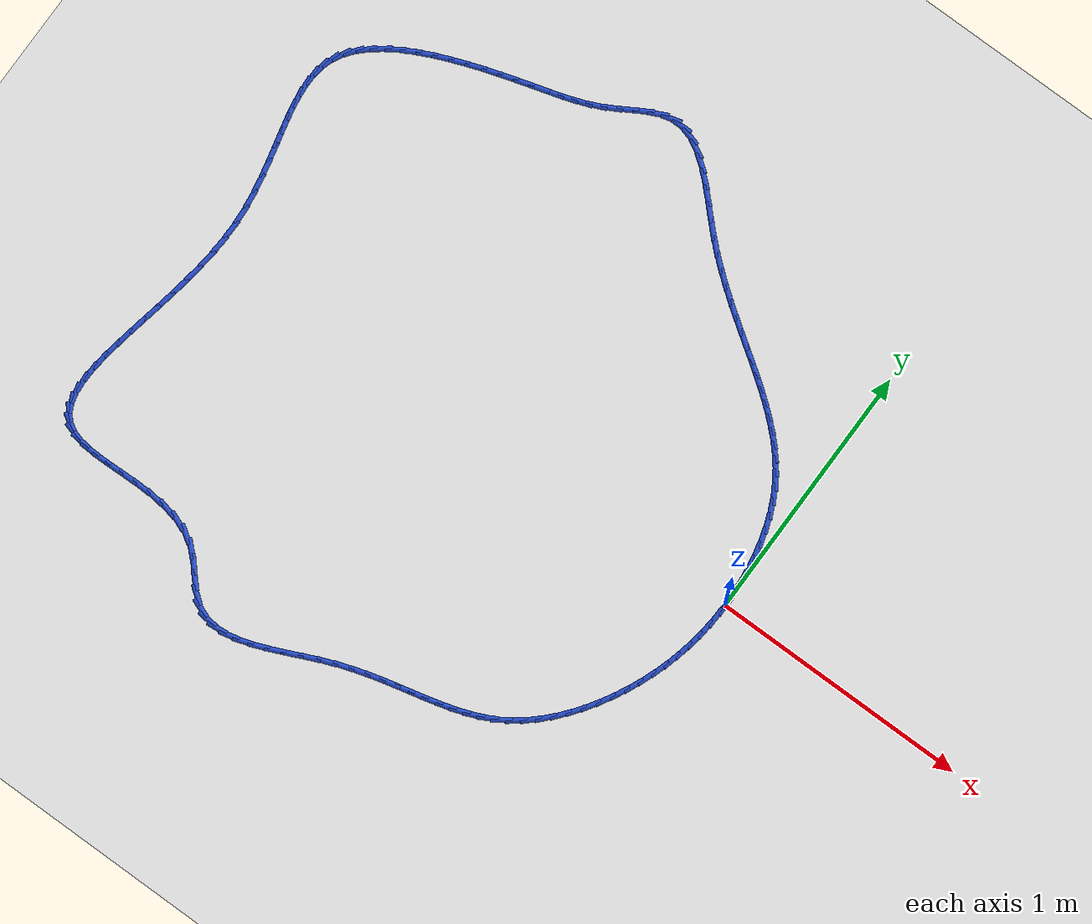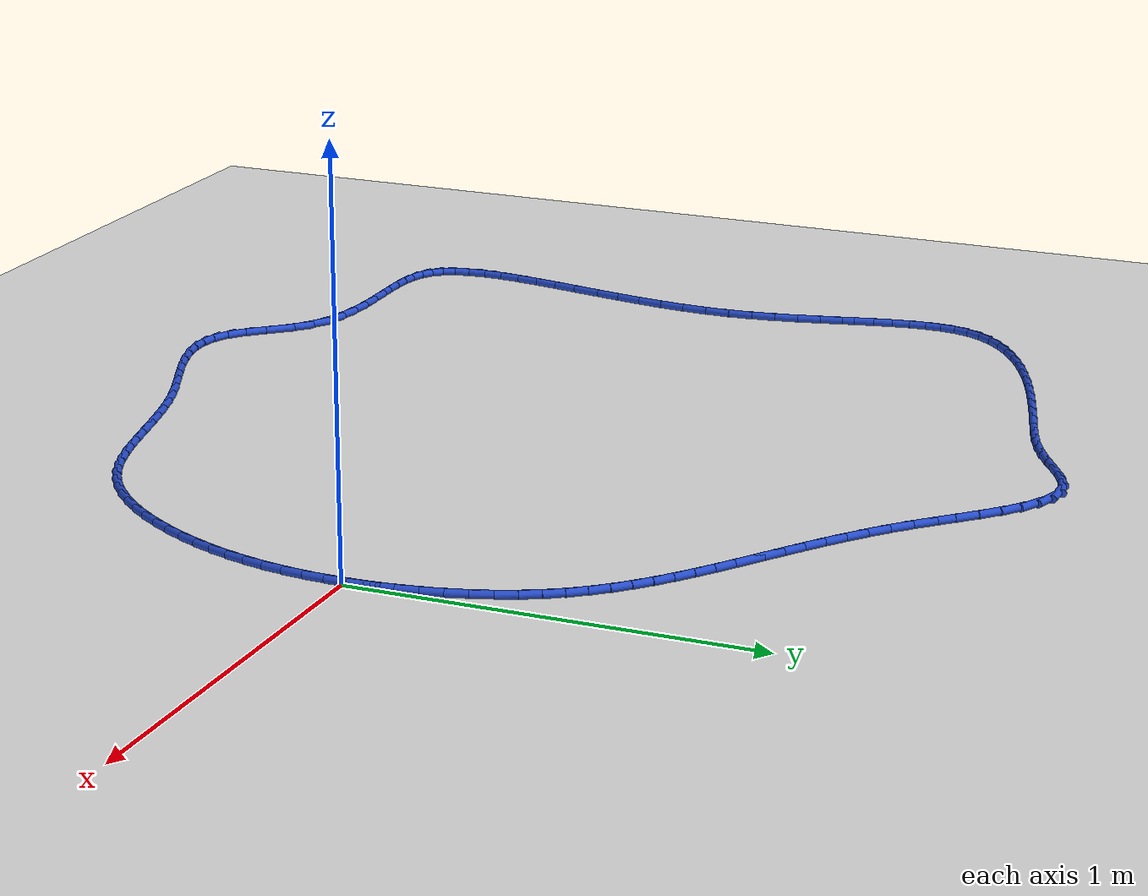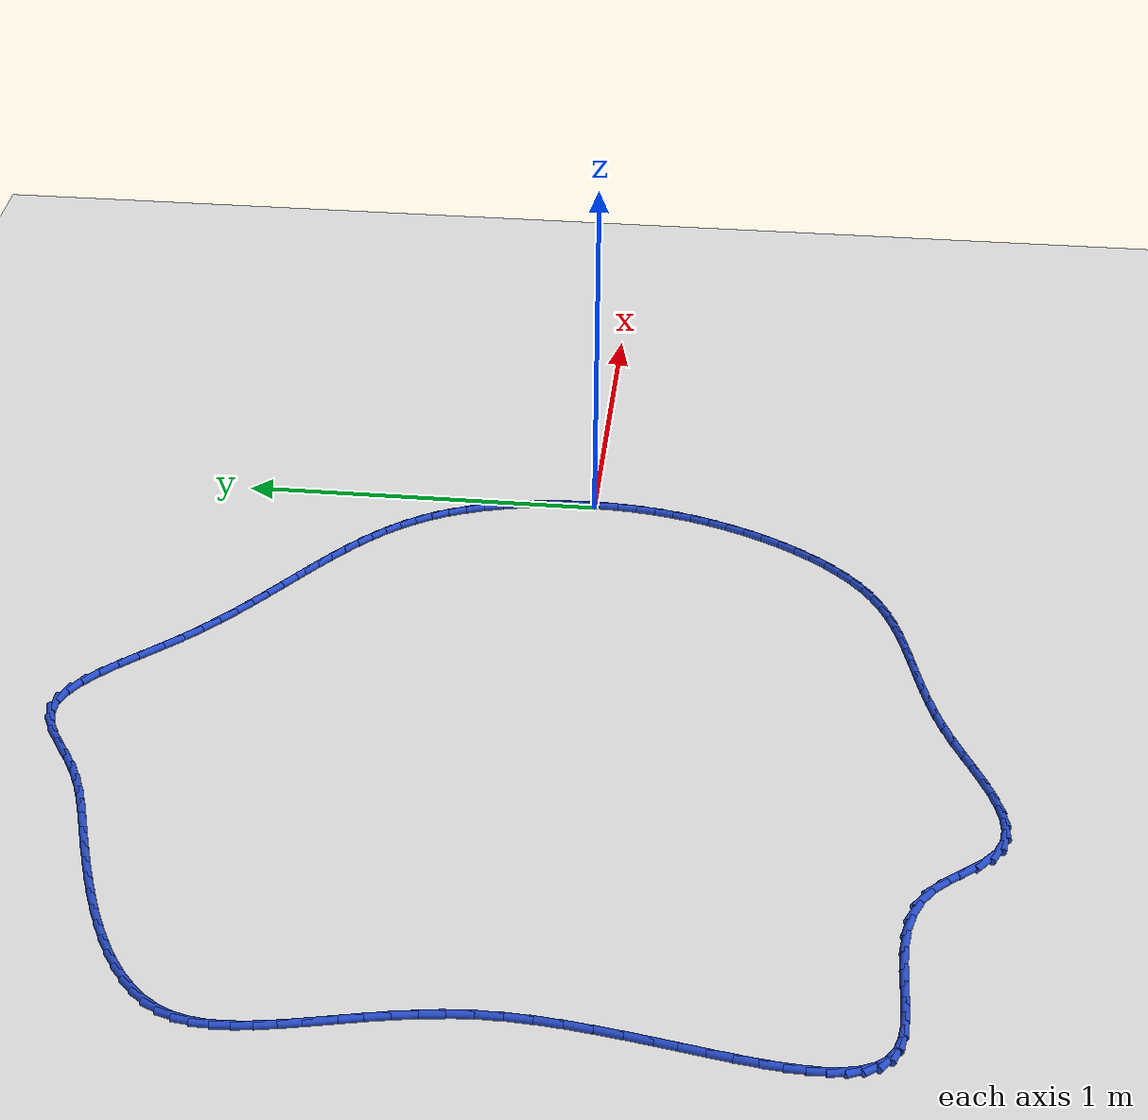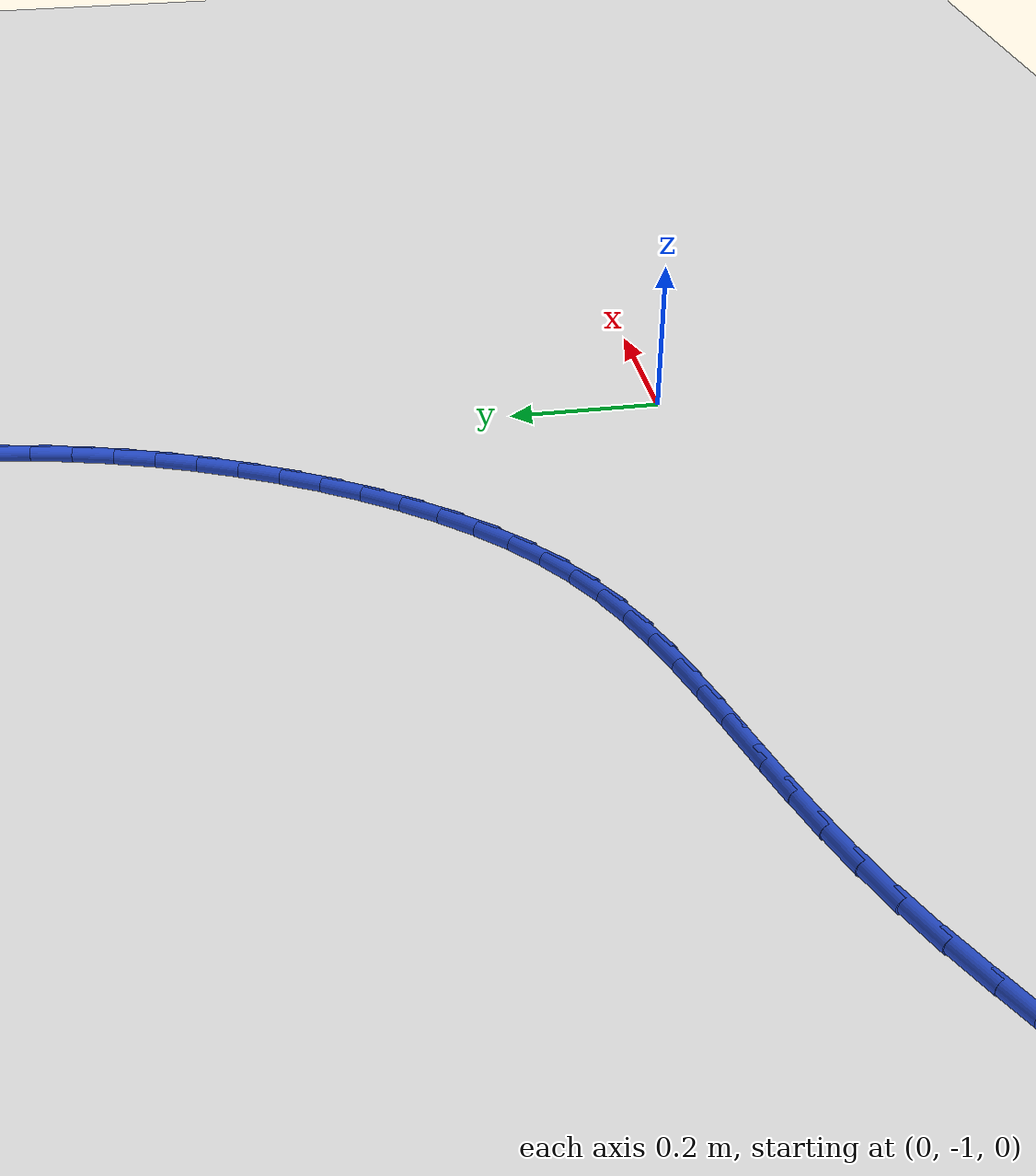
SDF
<sdf version="1.6">
 <world name="default">
  <light name="sun" type="directional">
   <pose>0 0 10 0 -0 0</pose>
   <diffuse>0.8 0.8 0.8 1</diffuse>
   <specular>0.2 0.2 0.2 1</specular>
   <attenuation>
    <range>1000</range>
    <constant>0.9</constant>
    <linear>0.01</linear>
    <quadratic>0.001</quadratic>
   </attenuation>
   <direction>-0.5 0.1 -0.9</direction>
  </light>
  <model name="ground_plane">
   <static>1</static>
   <link name="link">
    <collision name="collision">
     <geometry><plane><normal>0 0 1</normal><size>100 100</size></plane></geometry>
     <surface><friction><ode><mu>100</mu><mu2>50</mu2></ode></friction></surface>
    </collision>
    <visual name="visual">
     <cast_shadows>0</cast_shadows>
     <geometry><plane><normal>0 0 1</normal><size>100 100</size></plane></geometry>
     <material>
      <script><uri>file://media/materials/scripts/gazebo.material</uri><name>Gazebo/WhiteGlow</name></script>
     </material>
    </visual>
   </link>
  </model>
  <gravity>0 0 -9.8</gravity>
  <magnetic_field>6e-06 2.3e-05 -4.2e-05</magnetic_field>
  <atmosphere type="adiabatic"/>
  <physics name="default_physics" default="0" type="ode">
   <max_step_size>0.001</max_step_size>
   <real_time_factor>1</real_time_factor>
   <real_time_update_rate>1000</real_time_update_rate>
  </physics>
  <scene><ambient>0.4 0.4 0.4 1</ambient><background>0.7 0.7 0.7 1</background><shadows>1</shadows></scene>
  <spherical_coordinates>
   <surface_model>EARTH_WGS84</surface_model>
   <latitude_deg>0</latitude_deg>
   <longitude_deg>0</longitude_deg>
   <elevation>0</elevation>
   <heading_deg>0</heading_deg>
  </spherical_coordinates>
  <model name="line">
   <link name="link_0">
    <pose>-5.898059818321144e-17 -8.326672684688674e-17 0.01 0 1.57 -1.5503836142528844</pose>
    <collision name="collision">
     <geometry><cylinder><radius>0.01</radius><length>0.08</length></cylinder></geometry>
    </collision>
    <visual name="visual">
     <material>
      <script><name>Gazebo/Blue</name><uri>file://media/materials/scripts/gazebo.material</uri></script>
     </material>
     <geometry><cylinder><radius>0.01</radius><length>0.08</length></cylinder></geometry>
    </visual>
   </link>
   <link name="link_1">
    <pose>-0.0011329032678116374 0.05549217963258938 0.01 0 1.57 -1.4979796829378895</pose>
    <collision name="collision">
     <geometry><cylinder><radius>0.01</radius><length>0.08</length></cylinder></geometry>
    </collision>
    <visual name="visual">
     <material>
      <script><name>Gazebo/Blue</name><uri>file://media/materials/scripts/gazebo.material</uri></script>
     </material>
     <geometry><cylinder><radius>0.01</radius><length>0.08</length></cylinder></geometry>
    </visual>
   </link>
   <link name="link_2">
    <pose>-0.005194142887330147 0.11116707681520731 0.01 0 1.57 -1.4445548681406772</pose>
    <collision name="collision">
     <geometry><cylinder><radius>0.01</radius><length>0.08</length></cylinder></geometry>
    </collision>
    <visual name="visual">
     <material>
      <script><name>Gazebo/Blue</name><uri>file://media/materials/scripts/gazebo.material</uri></script>
     </material>
     <geometry><cylinder><radius>0.01</radius><length>0.08</length></cylinder></geometry>
    </visual>
   </link>
   <link name="link_3">
    <pose>-0.012225290778290552 0.1665669164549131 0.01 0 1.57 -1.3891165430512056</pose>
    <collision name="collision">
     <geometry><cylinder><radius>0.01</radius><length>0.08</length></cylinder></geometry>
    </collision>
    <visual name="visual">
     <material>
      <script><name>Gazebo/Blue</name><uri>file://media/materials/scripts/gazebo.material</uri></script>
     </material>
     <geometry><cylinder><radius>0.01</radius><length>0.08</length></cylinder></geometry>
    </visual>
   </link>
   <link name="link_4">
    <pose>-0.02226791886042784 0.22123392345876614 0.01 0 1.57 -1.3306355662528466</pose>
    <collision name="collision">
     <geometry><cylinder><radius>0.01</radius><length>0.08</length></cylinder></geometry>
    </collision>
    <visual name="visual">
     <material>
      <script><name>Gazebo/Blue</name><uri>file://media/materials/scripts/gazebo.material</uri></script>
     </material>
     <geometry><cylinder><radius>0.01</radius><length>0.08</length></cylinder></geometry>
    </visual>
   </link>
   <link name="link_5">
    <pose>-0.03536359905347698 0.27471032273382595 0.01 0 1.57 -1.2680160669781582</pose>
    <collision name="collision">
     <geometry><cylinder><radius>0.01</radius><length>0.08</length></cylinder></geometry>
    </collision>
    <visual name="visual">
     <material>
      <script><name>Gazebo/Blue</name><uri>file://media/materials/scripts/gazebo.material</uri></script>
     </material>
     <geometry><cylinder><radius>0.01</radius><length>0.08</length></cylinder></geometry>
    </visual>
   </link>
   <link name="link_6">
    <pose>-0.05155390327717296 0.32653833918715197 0.01 0 1.57 -1.2000758719438602</pose>
    <collision name="collision">
     <geometry><cylinder><radius>0.01</radius><length>0.08</length></cylinder></geometry>
    </collision>
    <visual name="visual">
     <material>
      <script><name>Gazebo/Blue</name><uri>file://media/materials/scripts/gazebo.material</uri></script>
     </material>
     <geometry><cylinder><radius>0.01</radius><length>0.08</length></cylinder></geometry>
    </visual>
   </link>
   <link name="link_7">
    <pose>-0.07088040345125075 0.37626019772580344 0.01 0 1.57 -1.1255457795786277</pose>
    <collision name="collision">
     <geometry><cylinder><radius>0.01</radius><length>0.08</length></cylinder></geometry>
    </collision>
    <visual name="visual">
     <material>
      <script><name>Gazebo/Blue</name><uri>file://media/materials/scripts/gazebo.material</uri></script>
     </material>
     <geometry><cylinder><radius>0.01</radius><length>0.08</length></cylinder></geometry>
    </visual>
   </link>
   <link name="link_8">
    <pose>-0.09338467149544535 0.4234181232568401 0.01 0 1.57 -1.044061323672254</pose>
    <collision name="collision">
     <geometry><cylinder><radius>0.01</radius><length>0.08</length></cylinder></geometry>
    </collision>
    <visual name="visual">
     <material>
      <script><name>Gazebo/Blue</name><uri>file://media/materials/scripts/gazebo.material</uri></script>
     </material>
     <geometry><cylinder><radius>0.01</radius><length>0.08</length></cylinder></geometry>
    </visual>
   </link>
   <link name="link_9">
    <pose>-0.11908711650836779 0.46761537002746734 0.01 0 1.57 -0.9631357885905049</pose>
    <collision name="collision">
     <geometry><cylinder><radius>0.01</radius><length>0.08</length></cylinder></geometry>
    </collision>
    <visual name="visual">
     <material>
      <script><name>Gazebo/Blue</name><uri>file://media/materials/scripts/gazebo.material</uri></script>
     </material>
     <geometry><cylinder><radius>0.01</radius><length>0.08</length></cylinder></geometry>
    </visual>
   </link>
   <link name="link_10">
    <pose>-0.147835367976142 0.5089534541035359 0.01 0 1.57 -0.8882764612524884</pose>
    <collision name="collision">
     <geometry><cylinder><radius>0.01</radius><length>0.08</length></cylinder></geometry>
    </collision>
    <visual name="visual">
     <material>
      <script><name>Gazebo/Blue</name><uri>file://media/materials/scripts/gazebo.material</uri></script>
     </material>
     <geometry><cylinder><radius>0.01</radius><length>0.08</length></cylinder></geometry>
    </visual>
   </link>
   <link name="link_11">
    <pose>-0.17939270947056035 0.5477771282850519 0.01 0 1.57 -0.8210759511633126</pose>
    <collision name="collision">
     <geometry><cylinder><radius>0.01</radius><length>0.08</length></cylinder></geometry>
    </collision>
    <visual name="visual">
     <material>
      <script><name>Gazebo/Blue</name><uri>file://media/materials/scripts/gazebo.material</uri></script>
     </material>
     <geometry><cylinder><radius>0.01</radius><length>0.08</length></cylinder></geometry>
    </visual>
   </link>
   <link name="link_12">
    <pose>-0.2135218541390313 0.5844327903617667 0.01 0 1.57 -0.7625456823559136</pose>
    <collision name="collision">
     <geometry><cylinder><radius>0.01</radius><length>0.08</length></cylinder></geometry>
    </collision>
    <visual name="visual">
     <material>
      <script><name>Gazebo/Blue</name><uri>file://media/materials/scripts/gazebo.material</uri></script>
     </material>
     <geometry><cylinder><radius>0.01</radius><length>0.08</length></cylinder></geometry>
    </visual>
   </link>
   <link name="link_13">
    <pose>-0.2499855151289634 0.6192668381234329 0.01 0 1.57 -0.7131924407427168</pose>
    <collision name="collision">
     <geometry><cylinder><radius>0.01</radius><length>0.08</length></cylinder></geometry>
    </collision>
    <visual name="visual">
     <material>
      <script><name>Gazebo/Blue</name><uri>file://media/materials/scripts/gazebo.material</uri></script>
     </material>
     <geometry><cylinder><radius>0.01</radius><length>0.08</length></cylinder></geometry>
    </visual>
   </link>
   <link name="link_14">
    <pose>-0.288546405587765 0.6526256693598027 0.01 0 1.57 -0.6731299744752797</pose>
    <collision name="collision">
     <geometry><cylinder><radius>0.01</radius><length>0.08</length></cylinder></geometry>
    </collision>
    <visual name="visual">
     <material>
      <script><name>Gazebo/Blue</name><uri>file://media/materials/scripts/gazebo.material</uri></script>
     </material>
     <geometry><cylinder><radius>0.01</radius><length>0.08</length></cylinder></geometry>
    </visual>
   </link>
   <link name="link_15">
    <pose>-0.3289672386628448 0.6848556818606286 0.01 0 1.57 -0.6422055719112713</pose>
    <collision name="collision">
     <geometry><cylinder><radius>0.01</radius><length>0.08</length></cylinder></geometry>
    </collision>
    <visual name="visual">
     <material>
      <script><name>Gazebo/Blue</name><uri>file://media/materials/scripts/gazebo.material</uri></script>
     </material>
     <geometry><cylinder><radius>0.01</radius><length>0.08</length></cylinder></geometry>
    </visual>
   </link>
   <link name="link_16">
    <pose>-0.3710107275016111 0.7163032734156626 0.01 0 1.57 -0.6201115737771121</pose>
    <collision name="collision">
     <geometry><cylinder><radius>0.01</radius><length>0.08</length></cylinder></geometry>
    </collision>
    <visual name="visual">
     <material>
      <script><name>Gazebo/Blue</name><uri>file://media/materials/scripts/gazebo.material</uri></script>
     </material>
     <geometry><cylinder><radius>0.01</radius><length>0.08</length></cylinder></geometry>
    </visual>
   </link>
   <link name="link_17">
    <pose>-0.4144395852514726 0.7473148418146566 0.01 0 1.57 -0.6064688919162905</pose>
    <collision name="collision">
     <geometry><cylinder><radius>0.01</radius><length>0.08</length></cylinder></geometry>
    </collision>
    <visual name="visual">
     <material>
      <script><name>Gazebo/Blue</name><uri>file://media/materials/scripts/gazebo.material</uri></script>
     </material>
     <geometry><cylinder><radius>0.01</radius><length>0.08</length></cylinder></geometry>
    </visual>
   </link>
   <link name="link_18">
    <pose>-0.4590165250598377 0.7782367848473632 0.01 0 1.57 -0.6008812202760785</pose>
    <collision name="collision">
     <geometry><cylinder><radius>0.01</radius><length>0.08</length></cylinder></geometry>
    </collision>
    <visual name="visual">
     <material>
      <script><name>Gazebo/Blue</name><uri>file://media/materials/scripts/gazebo.material</uri></script>
     </material>
     <geometry><cylinder><radius>0.01</radius><length>0.08</length></cylinder></geometry>
    </visual>
   </link>
   <link name="link_19">
    <pose>-0.5045042600741151 0.8094155003035346 0.01 0 1.57 -0.6029641579892127</pose>
    <collision name="collision">
     <geometry><cylinder><radius>0.01</radius><length>0.08</length></cylinder></geometry>
    </collision>
    <visual name="visual">
     <material>
      <script><name>Gazebo/Blue</name><uri>file://media/materials/scripts/gazebo.material</uri></script>
     </material>
     <geometry><cylinder><radius>0.01</radius><length>0.08</length></cylinder></geometry>
    </visual>
   </link>
   <link name="link_20">
    <pose>-0.5506655034417127 0.8411973859729224 0.01 0 1.57 -0.6123549243584733</pose>
    <collision name="collision">
     <geometry><cylinder><radius>0.01</radius><length>0.08</length></cylinder></geometry>
    </collision>
    <visual name="visual">
     <material>
      <script><name>Gazebo/Blue</name><uri>file://media/materials/scripts/gazebo.material</uri></script>
     </material>
     <geometry><cylinder><radius>0.01</radius><length>0.08</length></cylinder></geometry>
    </visual>
   </link>
   <link name="link_21">
    <pose>-0.5972629683100397 0.8739288396452795 0.01 0 1.57 -0.6287078698892908</pose>
    <collision name="collision">
     <geometry><cylinder><radius>0.01</radius><length>0.08</length></cylinder></geometry>
    </collision>
    <visual name="visual">
     <material>
      <script><name>Gazebo/Blue</name><uri>file://media/materials/scripts/gazebo.material</uri></script>
     </material>
     <geometry><cylinder><radius>0.01</radius><length>0.08</length></cylinder></geometry>
    </visual>
   </link>
   <link name="link_22">
    <pose>-0.644059367826504 0.9079562591103575 0.01 0 1.57 -0.6516800097753971</pose>
    <collision name="collision">
     <geometry><cylinder><radius>0.01</radius><length>0.08</length></cylinder></geometry>
    </collision>
    <visual name="visual">
     <material>
      <script><name>Gazebo/Blue</name><uri>file://media/materials/scripts/gazebo.material</uri></script>
     </material>
     <geometry><cylinder><radius>0.01</radius><length>0.08</length></cylinder></geometry>
    </visual>
   </link>
   <link name="link_23">
    <pose>-0.6908174151385146 0.9436260421579092 0.01 0 1.57 -0.680910064861538</pose>
    <collision name="collision">
     <geometry><cylinder><radius>0.01</radius><length>0.08</length></cylinder></geometry>
    </collision>
    <visual name="visual">
     <material>
      <script><name>Gazebo/Blue</name><uri>file://media/materials/scripts/gazebo.material</uri></script>
     </material>
     <geometry><cylinder><radius>0.01</radius><length>0.08</length></cylinder></geometry>
    </visual>
   </link>
   <link name="link_24">
    <pose>-0.7372998233934798 0.9812845865776866 0.01 0 1.57 -0.7159942586551378</pose>
    <collision name="collision">
     <geometry><cylinder><radius>0.01</radius><length>0.08</length></cylinder></geometry>
    </collision>
    <visual name="visual">
     <material>
      <script><name>Gazebo/Blue</name><uri>file://media/materials/scripts/gazebo.material</uri></script>
     </material>
     <geometry><cylinder><radius>0.01</radius><length>0.08</length></cylinder></geometry>
    </visual>
   </link>
   <link name="link_25">
    <pose>-0.7832693057388078 1.0212782901594415 0.01 0 1.57 -0.7561793472187902</pose>
    <collision name="collision">
     <geometry><cylinder><radius>0.01</radius><length>0.08</length></cylinder></geometry>
    </collision>
    <visual name="visual">
     <material>
      <script><name>Gazebo/Blue</name><uri>file://media/materials/scripts/gazebo.material</uri></script>
     </material>
     <geometry><cylinder><radius>0.01</radius><length>0.08</length></cylinder></geometry>
    </visual>
   </link>
   <link name="link_26">
    <pose>-0.8284927329432289 1.0639332829966084 0.01 0 1.57 -0.7879725726900139</pose>
    <collision name="collision">
     <geometry><cylinder><radius>0.01</radius><length>0.08</length></cylinder></geometry>
    </collision>
    <visual name="visual">
     <material>
      <script><name>Gazebo/Blue</name><uri>file://media/materials/scripts/gazebo.material</uri></script>
     </material>
     <geometry><cylinder><radius>0.01</radius><length>0.08</length></cylinder></geometry>
    </visual>
   </link>
   <link name="link_27">
    <pose>-0.872935917424615 1.1086058885026884 0.01 0 1.57 -0.793965645127022</pose>
    <collision name="collision">
     <geometry><cylinder><radius>0.01</radius><length>0.08</length></cylinder></geometry>
    </collision>
    <visual name="visual">
     <material>
      <script><name>Gazebo/Blue</name><uri>file://media/materials/scripts/gazebo.material</uri></script>
     </material>
     <geometry><cylinder><radius>0.01</radius><length>0.08</length></cylinder></geometry>
    </visual>
   </link>
   <link name="link_28">
    <pose>-0.9168470374378987 1.1532759446938583 0.01 0 1.57 -0.7725655730965395</pose>
    <collision name="collision">
     <geometry><cylinder><radius>0.01</radius><length>0.08</length></cylinder></geometry>
    </collision>
    <visual name="visual">
     <material>
      <script><name>Gazebo/Blue</name><uri>file://media/materials/scripts/gazebo.material</uri></script>
     </material>
     <geometry><cylinder><radius>0.01</radius><length>0.08</length></cylinder></geometry>
    </visual>
   </link>
   <link name="link_29">
    <pose>-0.9604957577724618 1.1958185463878352 0.01 0 1.57 -0.7200126690075901</pose>
    <collision name="collision">
     <geometry><cylinder><radius>0.01</radius><length>0.08</length></cylinder></geometry>
    </collision>
    <visual name="visual">
     <material>
      <script><name>Gazebo/Blue</name><uri>file://media/materials/scripts/gazebo.material</uri></script>
     </material>
     <geometry><cylinder><radius>0.01</radius><length>0.08</length></cylinder></geometry>
    </visual>
   </link>
   <link name="link_30">
    <pose>-1.0041517432176859 1.234108788402338 0.01 0 1.57 -0.6282268395394933</pose>
    <collision name="collision">
     <geometry><cylinder><radius>0.01</radius><length>0.08</length></cylinder></geometry>
    </collision>
    <visual name="visual">
     <material>
      <script><name>Gazebo/Blue</name><uri>file://media/materials/scripts/gazebo.material</uri></script>
     </material>
     <geometry><cylinder><radius>0.01</radius><length>0.08</length></cylinder></geometry>
    </visual>
   </link>
   <link name="link_31">
    <pose>-1.048084658562953 1.2660217655550843 0.01 0 1.57 -0.4844874124882894</pose>
    <collision name="collision">
     <geometry><cylinder><radius>0.01</radius><length>0.08</length></cylinder></geometry>
    </collision>
    <visual name="visual">
     <material>
      <script><name>Gazebo/Blue</name><uri>file://media/materials/scripts/gazebo.material</uri></script>
     </material>
     <geometry><cylinder><radius>0.01</radius><length>0.08</length></cylinder></geometry>
    </visual>
   </link>
   <link name="link_32">
    <pose>-1.0925641685976446 1.289432572663792 0.01 0 1.57 -0.2750734771516769</pose>
    <collision name="collision">
     <geometry><cylinder><radius>0.01</radius><length>0.08</length></cylinder></geometry>
    </collision>
    <visual name="visual">
     <material>
      <script><name>Gazebo/Blue</name><uri>file://media/materials/scripts/gazebo.material</uri></script>
     </material>
     <geometry><cylinder><radius>0.01</radius><length>0.08</length></cylinder></geometry>
    </visual>
   </link>
   <link name="link_33">
    <pose>-1.1378599381111432 1.3022163045461803 0.01 0 1.57 -0.0006990020422541509</pose>
    <collision name="collision">
     <geometry><cylinder><radius>0.01</radius><length>0.08</length></cylinder></geometry>
    </collision>
    <visual name="visual">
     <material>
      <script><name>Gazebo/Blue</name><uri>file://media/materials/scripts/gazebo.material</uri></script>
     </material>
     <geometry><cylinder><radius>0.01</radius><length>0.08</length></cylinder></geometry>
    </visual>
   </link>
   <link name="link_34">
    <pose>-1.1842415689011445 1.302248725406106 0.01 0 1.57 0.27496560778712964</pose>
    <collision name="collision">
     <geometry><cylinder><radius>0.01</radius><length>0.08</length></cylinder></geometry>
    </collision>
    <visual name="visual">
     <material>
      <script><name>Gazebo/Blue</name><uri>file://media/materials/scripts/gazebo.material</uri></script>
     </material>
     <geometry><cylinder><radius>0.01</radius><length>0.08</length></cylinder></geometry>
    </visual>
   </link>
   <link name="link_35">
    <pose>-1.231845650270529 1.2888190672866726 0.01 0 1.57 0.44589557251280154</pose>
    <collision name="collision">
     <geometry><cylinder><radius>0.01</radius><length>0.08</length></cylinder></geometry>
    </collision>
    <visual name="visual">
     <material>
      <script><name>Gazebo/Blue</name><uri>file://media/materials/scripts/gazebo.material</uri></script>
     </material>
     <geometry><cylinder><radius>0.01</radius><length>0.08</length></cylinder></geometry>
    </visual>
   </link>
   <link name="link_36">
    <pose>-1.280395118280809 1.2656122812502482 0.01 0 1.57 0.5247782048721744</pose>
    <collision name="collision">
     <geometry><cylinder><radius>0.01</radius><length>0.08</length></cylinder></geometry>
    </collision>
    <visual name="visual">
     <material>
      <script><name>Gazebo/Blue</name><uri>file://media/materials/scripts/gazebo.material</uri></script>
     </material>
     <geometry><cylinder><radius>0.01</radius><length>0.08</length></cylinder></geometry>
    </visual>
   </link>
   <link name="link_37">
    <pose>-1.3295327304025144 1.2371653425236029 0.01 0 1.57 0.5333750159718375</pose>
    <collision name="collision">
     <geometry><cylinder><radius>0.01</radius><length>0.08</length></cylinder></geometry>
    </collision>
    <visual name="visual">
     <material>
      <script><name>Gazebo/Blue</name><uri>file://media/materials/scripts/gazebo.material</uri></script>
     </material>
     <geometry><cylinder><radius>0.01</radius><length>0.08</length></cylinder></geometry>
    </visual>
   </link>
   <link name="link_38">
    <pose>-1.3789012441061739 1.2080152263335109 0.01 0 1.57 0.4787702765543212</pose>
    <collision name="collision">
     <geometry><cylinder><radius>0.01</radius><length>0.08</length></cylinder></geometry>
    </collision>
    <visual name="visual">
     <material>
      <script><name>Gazebo/Blue</name><uri>file://media/materials/scripts/gazebo.material</uri></script>
     </material>
     <geometry><cylinder><radius>0.01</radius><length>0.08</length></cylinder></geometry>
    </visual>
   </link>
   <link name="link_39">
    <pose>-1.4281850783597936 1.182434510265762 0.01 0 1.57 0.4028777444398364</pose>
    <collision name="collision">
     <geometry><cylinder><radius>0.01</radius><length>0.08</length></cylinder></geometry>
    </collision>
    <visual name="visual">
     <material>
      <script><name>Gazebo/Blue</name><uri>file://media/materials/scripts/gazebo.material</uri></script>
     </material>
     <geometry><cylinder><radius>0.01</radius><length>0.08</length></cylinder></geometry>
    </visual>
   </link>
   <link name="link_40">
    <pose>-1.4775914315814827 1.161378040625954 0.01 0 1.57 0.3421307854269002</pose>
    <collision name="collision">
     <geometry><cylinder><radius>0.01</radius><length>0.08</length></cylinder></geometry>
    </collision>
    <visual name="visual">
     <material>
      <script><name>Gazebo/Blue</name><uri>file://media/materials/scripts/gazebo.material</uri></script>
     </material>
     <geometry><cylinder><radius>0.01</radius><length>0.08</length></cylinder></geometry>
    </visual>
   </link>
   <link name="link_41">
    <pose>-1.5276839903265291 1.143538272105965 0.01 0 1.57 0.3015986647448183</pose>
    <collision name="collision">
     <geometry><cylinder><radius>0.01</radius><length>0.08</length></cylinder></geometry>
    </collision>
    <visual name="visual">
     <material>
      <script><name>Gazebo/Blue</name><uri>file://media/materials/scripts/gazebo.material</uri></script>
     </material>
     <geometry><cylinder><radius>0.01</radius><length>0.08</length></cylinder></geometry>
    </visual>
   </link>
   <link name="link_42">
    <pose>-1.579033308563353 1.1275640765227992 0.01 0 1.57 0.2829256089147558</pose>
    <collision name="collision">
     <geometry><cylinder><radius>0.01</radius><length>0.08</length></cylinder></geometry>
    </collision>
    <visual name="visual">
     <material>
      <script><name>Gazebo/Blue</name><uri>file://media/materials/scripts/gazebo.material</uri></script>
     </material>
     <geometry><cylinder><radius>0.01</radius><length>0.08</length></cylinder></geometry>
    </visual>
   </link>
   <link name="link_43">
    <pose>-1.6322099402603745 1.1121043256934604 0.01 0 1.57 0.2831357448004341</pose>
    <collision name="collision">
     <geometry><cylinder><radius>0.01</radius><length>0.08</length></cylinder></geometry>
    </collision>
    <visual name="visual">
     <material>
      <script><name>Gazebo/Blue</name><uri>file://media/materials/scripts/gazebo.material</uri></script>
     </material>
     <geometry><cylinder><radius>0.01</radius><length>0.08</length></cylinder></geometry>
    </visual>
   </link>
   <link name="link_44">
    <pose>-1.6875894459589351 1.0959915237936977 0.01 0 1.57 0.2912530911735141</pose>
    <collision name="collision">
     <geometry><cylinder><radius>0.01</radius><length>0.08</length></cylinder></geometry>
    </collision>
    <visual name="visual">
     <material>
      <script><name>Gazebo/Blue</name><uri>file://media/materials/scripts/gazebo.material</uri></script>
     </material>
     <geometry><cylinder><radius>0.01</radius><length>0.08</length></cylinder></geometry>
    </visual>
   </link>
   <link name="link_45">
    <pose>-1.7446768704162947 1.078877971179829 0.01 0 1.57 0.30430173662034254</pose>
    <collision name="collision">
     <geometry><cylinder><radius>0.01</radius><length>0.08</length></cylinder></geometry>
    </collision>
    <visual name="visual">
     <material>
      <script><name>Gazebo/Blue</name><uri>file://media/materials/scripts/gazebo.material</uri></script>
     </material>
     <geometry><cylinder><radius>0.01</radius><length>0.08</length></cylinder></geometry>
    </visual>
   </link>
   <link name="link_46">
    <pose>-1.8027344265507268 1.0606446517286368 0.01 0 1.57 0.3224008881406608</pose>
    <collision name="collision">
     <geometry><cylinder><radius>0.01</radius><length>0.08</length></cylinder></geometry>
    </collision>
    <visual name="visual">
     <material>
      <script><name>Gazebo/Blue</name><uri>file://media/materials/scripts/gazebo.material</uri></script>
     </material>
     <geometry><cylinder><radius>0.01</radius><length>0.08</length></cylinder></geometry>
    </visual>
   </link>
   <link name="link_47">
    <pose>-1.8610243166068974 1.0411725593686258 0.01 0 1.57 0.3459764837701966</pose>
    <collision name="collision">
     <geometry><cylinder><radius>0.01</radius><length>0.08</length></cylinder></geometry>
    </collision>
    <visual name="visual">
     <material>
      <script><name>Gazebo/Blue</name><uri>file://media/materials/scripts/gazebo.material</uri></script>
     </material>
     <geometry><cylinder><radius>0.01</radius><length>0.08</length></cylinder></geometry>
    </visual>
   </link>
   <link name="link_48">
    <pose>-1.9188087428294711 1.0203426880283002 0.01 0 1.57 0.37577388343253787</pose>
    <collision name="collision">
     <geometry><cylinder><radius>0.01</radius><length>0.08</length></cylinder></geometry>
    </collision>
    <visual name="visual">
     <material>
      <script><name>Gazebo/Blue</name><uri>file://media/materials/scripts/gazebo.material</uri></script>
     </material>
     <geometry><cylinder><radius>0.01</radius><length>0.08</length></cylinder></geometry>
    </visual>
   </link>
   <link name="link_49">
    <pose>-1.9753499074631138 0.998036031636165 0.01 0 1.57 0.41290879181840157</pose>
    <collision name="collision">
     <geometry><cylinder><radius>0.01</radius><length>0.08</length></cylinder></geometry>
    </collision>
    <visual name="visual">
     <material>
      <script><name>Gazebo/Blue</name><uri>file://media/materials/scripts/gazebo.material</uri></script>
     </material>
     <geometry><cylinder><radius>0.01</radius><length>0.08</length></cylinder></geometry>
    </visual>
   </link>
   <link name="link_50">
    <pose>-2.0299100127524916 0.9741335841207245 0.01 0 1.57 0.45895499082207114</pose>
    <collision name="collision">
     <geometry><cylinder><radius>0.01</radius><length>0.08</length></cylinder></geometry>
    </collision>
    <visual name="visual">
     <material>
      <script><name>Gazebo/Blue</name><uri>file://media/materials/scripts/gazebo.material</uri></script>
     </material>
     <geometry><cylinder><radius>0.01</radius><length>0.08</length></cylinder></geometry>
    </visual>
   </link>
   <link name="link_51">
    <pose>-2.081751260942268 0.9485163394104834 0.01 0 1.57 0.5160668625350415</pose>
    <collision name="collision">
     <geometry><cylinder><radius>0.01</radius><length>0.08</length></cylinder></geometry>
    </collision>
    <visual name="visual">
     <material>
      <script><name>Gazebo/Blue</name><uri>file://media/materials/scripts/gazebo.material</uri></script>
     </material>
     <geometry><cylinder><radius>0.01</radius><length>0.08</length></cylinder></geometry>
    </visual>
   </link>
   <link name="link_52">
    <pose>-2.130135854277111 0.921065291433946 0.01 0 1.57 0.5871210532029238</pose>
    <collision name="collision">
     <geometry><cylinder><radius>0.01</radius><length>0.08</length></cylinder></geometry>
    </collision>
    <visual name="visual">
     <material>
      <script><name>Gazebo/Blue</name><uri>file://media/materials/scripts/gazebo.material</uri></script>
     </material>
     <geometry><cylinder><radius>0.01</radius><length>0.08</length></cylinder></geometry>
    </visual>
   </link>
   <link name="link_53">
    <pose>-2.1743259950016838 0.891661434119617 0.01 0 1.57 0.6758173249229327</pose>
    <collision name="collision">
     <geometry><cylinder><radius>0.01</radius><length>0.08</length></cylinder></geometry>
    </collision>
    <visual name="visual">
     <material>
      <script><name>Gazebo/Blue</name><uri>file://media/materials/scripts/gazebo.material</uri></script>
     </material>
     <geometry><cylinder><radius>0.01</radius><length>0.08</length></cylinder></geometry>
    </visual>
   </link>
   <link name="link_54">
    <pose>-2.213583885360653 0.8601857613960011 0.01 0 1.57 0.7865676334223154</pose>
    <collision name="collision">
     <geometry><cylinder><radius>0.01</radius><length>0.08</length></cylinder></geometry>
    </collision>
    <visual name="visual">
     <material>
      <script><name>Gazebo/Blue</name><uri>file://media/materials/scripts/gazebo.material</uri></script>
     </material>
     <geometry><cylinder><radius>0.01</radius><length>0.08</length></cylinder></geometry>
    </visual>
   </link>
   <link name="link_55">
    <pose>-2.2471717275986838 0.8265192671916023 0.01 0 1.57 0.9237865309065005</pose>
    <collision name="collision">
     <geometry><cylinder><radius>0.01</radius><length>0.08</length></cylinder></geometry>
    </collision>
    <visual name="visual">
     <material>
      <script><name>Gazebo/Blue</name><uri>file://media/materials/scripts/gazebo.material</uri></script>
     </material>
     <geometry><cylinder><radius>0.01</radius><length>0.08</length></cylinder></geometry>
    </visual>
   </link>
   <link name="link_56">
    <pose>-2.274351723960442 0.7905429454349258 0.01 0 1.57 1.0899460929267193</pose>
    <collision name="collision">
     <geometry><cylinder><radius>0.01</radius><length>0.08</length></cylinder></geometry>
    </collision>
    <visual name="visual">
     <material>
      <script><name>Gazebo/Blue</name><uri>file://media/materials/scripts/gazebo.material</uri></script>
     </material>
     <geometry><cylinder><radius>0.01</radius><length>0.08</length></cylinder></geometry>
    </visual>
   </link>
   <link name="link_57">
    <pose>-2.294387315599736 0.7521379255817454 0.01 0 1.57 1.272039974736983</pose>
    <collision name="collision">
     <geometry><cylinder><radius>0.01</radius><length>0.08</length></cylinder></geometry>
    </collision>
    <visual name="visual">
     <material>
      <script><name>Gazebo/Blue</name><uri>file://media/materials/scripts/gazebo.material</uri></script>
     </material>
     <geometry><cylinder><radius>0.01</radius><length>0.08</length></cylinder></geometry>
    </visual>
   </link>
   <link name="link_58">
    <pose>-2.3069847354021205 0.7112337751470994 0.01 0 1.57 1.4341497479571235</pose>
    <collision name="collision">
     <geometry><cylinder><radius>0.01</radius><length>0.08</length></cylinder></geometry>
    </collision>
    <visual name="visual">
     <material>
      <script><name>Gazebo/Blue</name><uri>file://media/materials/scripts/gazebo.material</uri></script>
     </material>
     <geometry><cylinder><radius>0.01</radius><length>0.08</length></cylinder></geometry>
    </visual>
   </link>
   <link name="link_59">
    <pose>-2.3129460391467562 0.6678799363646719 0.01 0 1.57 1.5643720903490415</pose>
    <collision name="collision">
     <geometry><cylinder><radius>0.01</radius><length>0.08</length></cylinder></geometry>
    </collision>
    <visual name="visual">
     <material>
      <script><name>Gazebo/Blue</name><uri>file://media/materials/scripts/gazebo.material</uri></script>
     </material>
     <geometry><cylinder><radius>0.01</radius><length>0.08</length></cylinder></geometry>
    </visual>
   </link>
   <link name="link_60">
    <pose>-2.3132398611833795 0.6221440739011687 0.01 0 1.57 -1.4793764221226882</pose>
    <collision name="collision">
     <geometry><cylinder><radius>0.01</radius><length>0.08</length></cylinder></geometry>
    </collision>
    <visual name="visual">
     <material>
      <script><name>Gazebo/Blue</name><uri>file://media/materials/scripts/gazebo.material</uri></script>
     </material>
     <geometry><cylinder><radius>0.01</radius><length>0.08</length></cylinder></geometry>
    </visual>
   </link>
   <link name="link_61">
    <pose>-2.308834835861724 0.5740938524232932 0.01 0 1.57 -1.4104407899527318</pose>
    <collision name="collision">
     <geometry><cylinder><radius>0.01</radius><length>0.08</length></cylinder></geometry>
    </collision>
    <visual name="visual">
     <material>
      <script><name>Gazebo/Blue</name><uri>file://media/materials/scripts/gazebo.material</uri></script>
     </material>
     <geometry><cylinder><radius>0.01</radius><length>0.08</length></cylinder></geometry>
    </visual>
   </link>
   <link name="link_62">
    <pose>-2.3006995975315254 0.5237969365977513 0.01 0 1.57 -1.3660525208758205</pose>
    <collision name="collision">
     <geometry><cylinder><radius>0.01</radius><length>0.08</length></cylinder></geometry>
    </collision>
    <visual name="visual">
     <material>
      <script><name>Gazebo/Blue</name><uri>file://media/materials/scripts/gazebo.material</uri></script>
     </material>
     <geometry><cylinder><radius>0.01</radius><length>0.08</length></cylinder></geometry>
    </visual>
   </link>
   <link name="link_63">
    <pose>-2.289802780542519 0.4713209910912472 0.01 0 1.57 -1.3423859269065108</pose>
    <collision name="collision">
     <geometry><cylinder><radius>0.01</radius><length>0.08</length></cylinder></geometry>
    </collision>
    <visual name="visual">
     <material>
      <script><name>Gazebo/Blue</name><uri>file://media/materials/scripts/gazebo.material</uri></script>
     </material>
     <geometry><cylinder><radius>0.01</radius><length>0.08</length></cylinder></geometry>
    </visual>
   </link>
   <link name="link_64">
    <pose>-2.277113019244438 0.4167336805704857 0.01 0 1.57 -1.3365435731937378</pose>
    <collision name="collision">
     <geometry><cylinder><radius>0.01</radius><length>0.08</length></cylinder></geometry>
    </collision>
    <visual name="visual">
     <material>
      <script><name>Gazebo/Blue</name><uri>file://media/materials/scripts/gazebo.material</uri></script>
     </material>
     <geometry><cylinder><radius>0.01</radius><length>0.08</length></cylinder></geometry>
    </visual>
   </link>
   <link name="link_65">
    <pose>-2.2635989479870195 0.36010266970217186 0.01 0 1.57 -1.346509229383936</pose>
    <collision name="collision">
     <geometry><cylinder><radius>0.01</radius><length>0.08</length></cylinder></geometry>
    </collision>
    <visual name="visual">
     <material>
      <script><name>Gazebo/Blue</name><uri>file://media/materials/scripts/gazebo.material</uri></script>
     </material>
     <geometry><cylinder><radius>0.01</radius><length>0.08</length></cylinder></geometry>
    </visual>
   </link>
   <link name="link_66">
    <pose>-2.2502292011199967 0.3014956231530094 0.01 0 1.57 -1.3709597286596942</pose>
    <collision name="collision">
     <geometry><cylinder><radius>0.01</radius><length>0.08</length></cylinder></geometry>
    </collision>
    <visual name="visual">
     <material>
      <script><name>Gazebo/Blue</name><uri>file://media/materials/scripts/gazebo.material</uri></script>
     </material>
     <geometry><cylinder><radius>0.01</radius><length>0.08</length></cylinder></geometry>
    </visual>
   </link>
   <link name="link_67">
    <pose>-2.237972412993105 0.24098020558970415 0.01 0 1.57 -1.4090431948801612</pose>
    <collision name="collision">
     <geometry><cylinder><radius>0.01</radius><length>0.08</length></cylinder></geometry>
    </collision>
    <visual name="visual">
     <material>
      <script><name>Gazebo/Blue</name><uri>file://media/materials/scripts/gazebo.material</uri></script>
     </material>
     <geometry><cylinder><radius>0.01</radius><length>0.08</length></cylinder></geometry>
    </visual>
   </link>
   <link name="link_68">
    <pose>-2.2277972179560797 0.17862408167896002 0.01 0 1.57 -1.4601467340829855</pose>
    <collision name="collision">
     <geometry><cylinder><radius>0.01</radius><length>0.08</length></cylinder></geometry>
    </collision>
    <visual name="visual">
     <material>
      <script><name>Gazebo/Blue</name><uri>file://media/materials/scripts/gazebo.material</uri></script>
     </material>
     <geometry><cylinder><radius>0.01</radius><length>0.08</length></cylinder></geometry>
    </visual>
   </link>
   <link name="link_69">
    <pose>-2.2206722503586556 0.11449491608748236 0.01 0 1.57 -1.5236305514877013</pose>
    <collision name="collision">
     <geometry><cylinder><radius>0.01</radius><length>0.08</length></cylinder></geometry>
    </collision>
    <visual name="visual">
     <material>
      <script><name>Gazebo/Blue</name><uri>file://media/materials/scripts/gazebo.material</uri></script>
     </material>
     <geometry><cylinder><radius>0.01</radius><length>0.08</length></cylinder></geometry>
    </visual>
   </link>
   <link name="link_70">
    <pose>-2.217564825250679 0.04866072856676281 0.01 0 1.57 1.5497219466868388</pose>
    <collision name="collision">
     <geometry><cylinder><radius>0.01</radius><length>0.08</length></cylinder></geometry>
    </collision>
    <visual name="visual">
     <material>
      <script><name>Gazebo/Blue</name><uri>file://media/materials/scripts/gazebo.material</uri></script>
     </material>
     <geometry><cylinder><radius>0.01</radius><length>0.08</length></cylinder></geometry>
    </visual>
   </link>
   <link name="link_71">
    <pose>-2.2189843516203163 -0.018687217373262205 0.01 0 1.57 1.4930124723782636</pose>
    <collision name="collision">
     <geometry><cylinder><radius>0.01</radius><length>0.08</length></cylinder></geometry>
    </collision>
    <visual name="visual">
     <material>
      <script><name>Gazebo/Blue</name><uri>file://media/materials/scripts/gazebo.material</uri></script>
     </material>
     <geometry><cylinder><radius>0.01</radius><length>0.08</length></cylinder></geometry>
    </visual>
   </link>
   <link name="link_72">
    <pose>-2.2243129541585684 -0.0870542537359261 0.01 0 1.57 1.4486768519576145</pose>
    <collision name="collision">
     <geometry><cylinder><radius>0.01</radius><length>0.08</length></cylinder></geometry>
    </collision>
    <visual name="visual">
     <material>
      <script><name>Gazebo/Blue</name><uri>file://media/materials/scripts/gazebo.material</uri></script>
     </material>
     <geometry><cylinder><radius>0.01</radius><length>0.08</length></cylinder></geometry>
    </visual>
   </link>
   <link name="link_73">
    <pose>-2.232762387625798 -0.15589985807463264 0.01 0 1.57 1.4153089551539115</pose>
    <collision name="collision">
     <geometry><cylinder><radius>0.01</radius><length>0.08</length></cylinder></geometry>
    </collision>
    <visual name="visual">
     <material>
      <script><name>Gazebo/Blue</name><uri>file://media/materials/scripts/gazebo.material</uri></script>
     </material>
     <geometry><cylinder><radius>0.01</radius><length>0.08</length></cylinder></geometry>
    </visual>
   </link>
   <link name="link_74">
    <pose>-2.2435444067823624 -0.22468350794278227 0.01 0 1.57 1.391939915161894</pose>
    <collision name="collision">
     <geometry><cylinder><radius>0.01</radius><length>0.08</length></cylinder></geometry>
    </collision>
    <visual name="visual">
     <material>
      <script><name>Gazebo/Blue</name><uri>file://media/materials/scripts/gazebo.material</uri></script>
     </material>
     <geometry><cylinder><radius>0.01</radius><length>0.08</length></cylinder></geometry>
    </visual>
   </link>
   <link name="link_75">
    <pose>-2.255870766388623 -0.2928646808937789 0.01 0 1.57 1.3780691913912964</pose>
    <collision name="collision">
     <geometry><cylinder><radius>0.01</radius><length>0.08</length></cylinder></geometry>
    </collision>
    <visual name="visual">
     <material>
      <script><name>Gazebo/Blue</name><uri>file://media/materials/scripts/gazebo.material</uri></script>
     </material>
     <geometry><cylinder><radius>0.01</radius><length>0.08</length></cylinder></geometry>
    </visual>
   </link>
   <link name="link_76">
    <pose>-2.26895322120494 -0.3599028544810249 0.01 0 1.57 1.3737042416038991</pose>
    <collision name="collision">
     <geometry><cylinder><radius>0.01</radius><length>0.08</length></cylinder></geometry>
    </collision>
    <visual name="visual">
     <material>
      <script><name>Gazebo/Blue</name><uri>file://media/materials/scripts/gazebo.material</uri></script>
     </material>
     <geometry><cylinder><radius>0.01</radius><length>0.08</length></cylinder></geometry>
    </visual>
   </link>
   <link name="link_77">
    <pose>-2.2820035259916733 -0.42525750625792347 0.01 0 1.57 1.3794426664822372</pose>
    <collision name="collision">
     <geometry><cylinder><radius>0.01</radius><length>0.08</length></cylinder></geometry>
    </collision>
    <visual name="visual">
     <material>
      <script><name>Gazebo/Blue</name><uri>file://media/materials/scripts/gazebo.material</uri></script>
     </material>
     <geometry><cylinder><radius>0.01</radius><length>0.08</length></cylinder></geometry>
    </visual>
   </link>
   <link name="link_78">
    <pose>-2.2942334355091822 -0.4883881137778778 0.01 0 1.57 1.3966312217301124</pose>
    <collision name="collision">
     <geometry><cylinder><radius>0.01</radius><length>0.08</length></cylinder></geometry>
    </collision>
    <visual name="visual">
     <material>
      <script><name>Gazebo/Blue</name><uri>file://media/materials/scripts/gazebo.material</uri></script>
     </material>
     <geometry><cylinder><radius>0.01</radius><length>0.08</length></cylinder></geometry>
    </visual>
   </link>
   <link name="link_79">
    <pose>-2.3048547045178283 -0.5487541545942889 0.01 0 1.57 1.4276488623232615</pose>
    <collision name="collision">
     <geometry><cylinder><radius>0.01</radius><length>0.08</length></cylinder></geometry>
    </collision>
    <visual name="visual">
     <material>
      <script><name>Gazebo/Blue</name><uri>file://media/materials/scripts/gazebo.material</uri></script>
     </material>
     <geometry><cylinder><radius>0.01</radius><length>0.08</length></cylinder></geometry>
    </visual>
   </link>
   <link name="link_80">
    <pose>-2.3130790877779694 -0.6058151062605601 0.01 0 1.57 1.4763823838622685</pose>
    <collision name="collision">
     <geometry><cylinder><radius>0.01</radius><length>0.08</length></cylinder></geometry>
    </collision>
    <visual name="visual">
     <material>
      <script><name>Gazebo/Blue</name><uri>file://media/materials/scripts/gazebo.material</uri></script>
     </material>
     <geometry><cylinder><radius>0.01</radius><length>0.08</length></cylinder></geometry>
    </visual>
   </link>
   <link name="link_81">
    <pose>-2.3181183400499674 -0.6590304463300944 0.01 0 1.57 1.5489711347403252</pose>
    <collision name="collision">
     <geometry><cylinder><radius>0.01</radius><length>0.08</length></cylinder></geometry>
    </collision>
    <visual name="visual">
     <material>
      <script><name>Gazebo/Blue</name><uri>file://media/materials/scripts/gazebo.material</uri></script>
     </material>
     <geometry><cylinder><radius>0.01</radius><length>0.08</length></cylinder></geometry>
    </visual>
   </link>
   <link name="link_82">
    <pose>-2.319184216094182 -0.7078596523562952 0.01 0 1.57 -1.4868136749743084</pose>
    <collision name="collision">
     <geometry><cylinder><radius>0.01</radius><length>0.08</length></cylinder></geometry>
    </collision>
    <visual name="visual">
     <material>
      <script><name>Gazebo/Blue</name><uri>file://media/materials/scripts/gazebo.material</uri></script>
     </material>
     <geometry><cylinder><radius>0.01</radius><length>0.08</length></cylinder></geometry>
    </visual>
   </link>
   <link name="link_83">
    <pose>-2.3154884706709735 -0.7517622018925638 0.01 0 1.57 -1.3347317657261517</pose>
    <collision name="collision">
     <geometry><cylinder><radius>0.01</radius><length>0.08</length></cylinder></geometry>
    </collision>
    <visual name="visual">
     <material>
      <script><name>Gazebo/Blue</name><uri>file://media/materials/scripts/gazebo.material</uri></script>
     </material>
     <geometry><cylinder><radius>0.01</radius><length>0.08</length></cylinder></geometry>
    </visual>
   </link>
   <link name="link_84">
    <pose>-2.3062428585407 -0.7901975724923032 0.01 0 1.57 -1.122814215778279</pose>
    <collision name="collision">
     <geometry><cylinder><radius>0.01</radius><length>0.08</length></cylinder></geometry>
    </collision>
    <visual name="visual">
     <material>
      <script><name>Gazebo/Blue</name><uri>file://media/materials/scripts/gazebo.material</uri></script>
     </material>
     <geometry><cylinder><radius>0.01</radius><length>0.08</length></cylinder></geometry>
    </visual>
   </link>
   <link name="link_85">
    <pose>-2.290659134463724 -0.8226252417089164 0.01 0 1.57 -0.850533203535557</pose>
    <collision name="collision">
     <geometry><cylinder><radius>0.01</radius><length>0.08</length></cylinder></geometry>
    </collision>
    <visual name="visual">
     <material>
      <script><name>Gazebo/Blue</name><uri>file://media/materials/scripts/gazebo.material</uri></script>
     </material>
     <geometry><cylinder><radius>0.01</radius><length>0.08</length></cylinder></geometry>
    </visual>
   </link>
   <link name="link_86">
    <pose>-2.267949053200404 -0.8485046870958062 0.01 0 1.57 -0.5503453597935779</pose>
    <collision name="collision">
     <geometry><cylinder><radius>0.01</radius><length>0.08</length></cylinder></geometry>
    </collision>
    <visual name="visual">
     <material>
      <script><name>Gazebo/Blue</name><uri>file://media/materials/scripts/gazebo.material</uri></script>
     </material>
     <geometry><cylinder><radius>0.01</radius><length>0.08</length></cylinder></geometry>
    </visual>
   </link>
   <link name="link_87">
    <pose>-2.237324375297296 -0.8672953920858765 0.01 0 1.57 -0.2888702083806845</pose>
    <collision name="collision">
     <geometry><cylinder><radius>0.01</radius><length>0.08</length></cylinder></geometry>
    </collision>
    <visual name="visual">
     <material>
      <script><name>Gazebo/Blue</name><uri>file://media/materials/scripts/gazebo.material</uri></script>
     </material>
     <geometry><cylinder><radius>0.01</radius><length>0.08</length></cylinder></geometry>
    </visual>
   </link>
   <link name="link_88">
    <pose>-2.1983973862531134 -0.8788638237225642 0.01 0 1.57 -0.12343449581295132</pose>
    <collision name="collision">
     <geometry><cylinder><radius>0.01</radius><length>0.08</length></cylinder></geometry>
    </collision>
    <visual name="visual">
     <material>
      <script><name>Gazebo/Blue</name><uri>file://media/materials/scripts/gazebo.material</uri></script>
     </material>
     <geometry><cylinder><radius>0.01</radius><length>0.08</length></cylinder></geometry>
    </visual>
   </link>
   <link name="link_89">
    <pose>-2.152266956518886 -0.8845870059022592 0.01 0 1.57 -0.03092737565999307</pose>
    <collision name="collision">
     <geometry><cylinder><radius>0.01</radius><length>0.08</length></cylinder></geometry>
    </collision>
    <visual name="visual">
     <material>
      <script><name>Gazebo/Blue</name><uri>file://media/materials/scripts/gazebo.material</uri></script>
     </material>
     <geometry><cylinder><radius>0.01</radius><length>0.08</length></cylinder></geometry>
    </visual>
   </link>
   <link name="link_90">
    <pose>-2.100376778408455 -0.8861923448033113 0.01 0 1.57 0.013967261046134263</pose>
    <collision name="collision">
     <geometry><cylinder><radius>0.01</radius><length>0.08</length></cylinder></geometry>
    </collision>
    <visual name="visual">
     <material>
      <script><name>Gazebo/Blue</name><uri>file://media/materials/scripts/gazebo.material</uri></script>
     </material>
     <geometry><cylinder><radius>0.01</radius><length>0.08</length></cylinder></geometry>
    </visual>
   </link>
   <link name="link_91">
    <pose>-2.0441705442356612 -0.8854072466040703 0.01 0 1.57 0.02450699996993845</pose>
    <collision name="collision">
     <geometry><cylinder><radius>0.01</radius><length>0.08</length></cylinder></geometry>
    </collision>
    <visual name="visual">
     <material>
      <script><name>Gazebo/Blue</name><uri>file://media/materials/scripts/gazebo.material</uri></script>
     </material>
     <geometry><cylinder><radius>0.01</radius><length>0.08</length></cylinder></geometry>
    </visual>
   </link>
   <link name="link_92">
    <pose>-1.9850919463143513 -0.8839591174828861 0.01 0 1.57 0.006342191996972328</pose>
    <collision name="collision">
     <geometry><cylinder><radius>0.01</radius><length>0.08</length></cylinder></geometry>
    </collision>
    <visual name="visual">
     <material>
      <script><name>Gazebo/Blue</name><uri>file://media/materials/scripts/gazebo.material</uri></script>
     </material>
     <geometry><cylinder><radius>0.01</radius><length>0.08</length></cylinder></geometry>
    </visual>
   </link>
   <link name="link_93">
    <pose>-1.9245846769583659 -0.8835753636181092 0.01 0 1.57 -0.03978620248419387</pose>
    <collision name="collision">
     <geometry><cylinder><radius>0.01</radius><length>0.08</length></cylinder></geometry>
    </collision>
    <visual name="visual">
     <material>
      <script><name>Gazebo/Blue</name><uri>file://media/materials/scripts/gazebo.material</uri></script>
     </material>
     <geometry><cylinder><radius>0.01</radius><length>0.08</length></cylinder></geometry>
    </visual>
   </link>
   <link name="link_94">
    <pose>-1.8640924284815474 -0.885983391188089 0.01 0 1.57 -0.11680954552356251</pose>
    <collision name="collision">
     <geometry><cylinder><radius>0.01</radius><length>0.08</length></cylinder></geometry>
    </collision>
    <visual name="visual">
     <material>
      <script><name>Gazebo/Blue</name><uri>file://media/materials/scripts/gazebo.material</uri></script>
     </material>
     <geometry><cylinder><radius>0.01</radius><length>0.08</length></cylinder></geometry>
    </visual>
   </link>
   <link name="link_95">
    <pose>-1.8050588931977372 -0.8929106063711756 0.01 0 1.57 -0.230524818899885</pose>
    <collision name="collision">
     <geometry><cylinder><radius>0.01</radius><length>0.08</length></cylinder></geometry>
    </collision>
    <visual name="visual">
     <material>
      <script><name>Gazebo/Blue</name><uri>file://media/materials/scripts/gazebo.material</uri></script>
     </material>
     <geometry><cylinder><radius>0.01</radius><length>0.08</length></cylinder></geometry>
    </visual>
   </link>
   <link name="link_96">
    <pose>-1.7489277634207807 -0.9060844153457189 0.01 0 1.57 -0.3877068874509017</pose>
    <collision name="collision">
     <geometry><cylinder><radius>0.01</radius><length>0.08</length></cylinder></geometry>
    </collision>
    <visual name="visual">
     <material>
      <script><name>Gazebo/Blue</name><uri>file://media/materials/scripts/gazebo.material</uri></script>
     </material>
     <geometry><cylinder><radius>0.01</radius><length>0.08</length></cylinder></geometry>
    </visual>
   </link>
   <link name="link_97">
    <pose>-1.6971427314645187 -0.927232224290069 0.01 0 1.57 -0.5895657920638186</pose>
    <collision name="collision">
     <geometry><cylinder><radius>0.01</radius><length>0.08</length></cylinder></geometry>
    </collision>
    <visual name="visual">
     <material>
      <script><name>Gazebo/Blue</name><uri>file://media/materials/scripts/gazebo.material</uri></script>
     </material>
     <geometry><cylinder><radius>0.01</radius><length>0.08</length></cylinder></geometry>
    </visual>
   </link>
   <link name="link_98">
    <pose>-1.6511152857938385 -0.9580212237366742 0.01 0 1.57 -0.7688654607259201</pose>
    <collision name="collision">
     <geometry><cylinder><radius>0.01</radius><length>0.08</length></cylinder></geometry>
    </collision>
    <visual name="visual">
     <material>
      <script><name>Gazebo/Blue</name><uri>file://media/materials/scripts/gazebo.material</uri></script>
     </material>
     <geometry><cylinder><radius>0.01</radius><length>0.08</length></cylinder></geometry>
    </visual>
   </link>
   <link name="link_99">
    <pose>-1.6106698079550097 -0.9971509878827792 0.01 0 1.57 -0.8432492629498087</pose>
    <collision name="collision">
     <geometry><cylinder><radius>0.01</radius><length>0.08</length></cylinder></geometry>
    </collision>
    <visual name="visual">
     <material>
      <script><name>Gazebo/Blue</name><uri>file://media/materials/scripts/gazebo.material</uri></script>
     </material>
     <geometry><cylinder><radius>0.01</radius><length>0.08</length></cylinder></geometry>
    </visual>
   </link>
   <link name="link_100">
    <pose>-1.5733509153279581 -1.0390583249448975 0.01 0 1.57 -0.8114136480187439</pose>
    <collision name="collision">
     <geometry><cylinder><radius>0.01</radius><length>0.08</length></cylinder></geometry>
    </collision>
    <visual name="visual">
     <material>
      <script><name>Gazebo/Blue</name><uri>file://media/materials/scripts/gazebo.material</uri></script>
     </material>
     <geometry><cylinder><radius>0.01</radius><length>0.08</length></cylinder></geometry>
    </visual>
   </link>
   <link name="link_101">
    <pose>-1.5365267689119004 -1.0778501001270668 0.01 0 1.57 -0.6528459598916048</pose>
    <collision name="collision">
     <geometry><cylinder><radius>0.01</radius><length>0.08</length></cylinder></geometry>
    </collision>
    <visual name="visual">
     <material>
      <script><name>Gazebo/Blue</name><uri>file://media/materials/scripts/gazebo.material</uri></script>
     </material>
     <geometry><cylinder><radius>0.01</radius><length>0.08</length></cylinder></geometry>
    </visual>
   </link>
   <link name="link_102">
    <pose>-1.4975688717427762 -1.1076413918162966 0.01 0 1.57 -0.37797686281688697</pose>
    <collision name="collision">
     <geometry><cylinder><radius>0.01</radius><length>0.08</length></cylinder></geometry>
    </collision>
    <visual name="visual">
     <material>
      <script><name>Gazebo/Blue</name><uri>file://media/materials/scripts/gazebo.material</uri></script>
     </material>
     <geometry><cylinder><radius>0.01</radius><length>0.08</length></cylinder></geometry>
    </visual>
   </link>
   <link name="link_103">
    <pose>-1.4547083953048225 -1.1246599464647504 0.01 0 1.57 -0.11519292361384192</pose>
    <collision name="collision">
     <geometry><cylinder><radius>0.01</radius><length>0.08</length></cylinder></geometry>
    </collision>
    <visual name="visual">
     <material>
      <script><name>Gazebo/Blue</name><uri>file://media/materials/scripts/gazebo.material</uri></script>
     </material>
     <geometry><cylinder><radius>0.01</radius><length>0.08</length></cylinder></geometry>
    </visual>
   </link>
   <link name="link_104">
    <pose>-1.4081746995394677 -1.1300441350217785 0.01 0 1.57 0.08862499889243677</pose>
    <collision name="collision">
     <geometry><cylinder><radius>0.01</radius><length>0.08</length></cylinder></geometry>
    </collision>
    <visual name="visual">
     <material>
      <script><name>Gazebo/Blue</name><uri>file://media/materials/scripts/gazebo.material</uri></script>
     </material>
     <geometry><cylinder><radius>0.01</radius><length>0.08</length></cylinder></geometry>
    </visual>
   </link>
   <link name="link_105">
    <pose>-1.3584803876949894 -1.1256284096878588 0.01 0 1.57 0.23227327961364172</pose>
    <collision name="collision">
     <geometry><cylinder><radius>0.01</radius><length>0.08</length></cylinder></geometry>
    </collision>
    <visual name="visual">
     <material>
      <script><name>Gazebo/Blue</name><uri>file://media/materials/scripts/gazebo.material</uri></script>
     </material>
     <geometry><cylinder><radius>0.01</radius><length>0.08</length></cylinder></geometry>
    </visual>
   </link>
   <link name="link_106">
    <pose>-1.3061380630196653 -1.1132472226634733 0.01 0 1.57 0.3275701207929217</pose>
    <collision name="collision">
     <geometry><cylinder><radius>0.01</radius><length>0.08</length></cylinder></geometry>
    </collision>
    <visual name="visual">
     <material>
      <script><name>Gazebo/Blue</name><uri>file://media/materials/scripts/gazebo.material</uri></script>
     </material>
     <geometry><cylinder><radius>0.01</radius><length>0.08</length></cylinder></geometry>
    </visual>
   </link>
   <link name="link_107">
    <pose>-1.251660328761772 -1.0947350261491011 0.01 0 1.57 0.38615665012714784</pose>
    <collision name="collision">
     <geometry><cylinder><radius>0.01</radius><length>0.08</length></cylinder></geometry>
    </collision>
    <visual name="visual">
     <material>
      <script><name>Gazebo/Blue</name><uri>file://media/materials/scripts/gazebo.material</uri></script>
     </material>
     <geometry><cylinder><radius>0.01</radius><length>0.08</length></cylinder></geometry>
    </visual>
   </link>
   <link name="link_108">
    <pose>-1.1955597881695879 -1.071926272345223 0.01 0 1.57 0.41594301858651594</pose>
    <collision name="collision">
     <geometry><cylinder><radius>0.01</radius><length>0.08</length></cylinder></geometry>
    </collision>
    <visual name="visual">
     <material>
      <script><name>Gazebo/Blue</name><uri>file://media/materials/scripts/gazebo.material</uri></script>
     </material>
     <geometry><cylinder><radius>0.01</radius><length>0.08</length></cylinder></geometry>
    </visual>
   </link>
   <link name="link_109">
    <pose>-1.1383490444913893 -1.046655413452318 0.01 0 1.57 0.4211948668331491</pose>
    <collision name="collision">
     <geometry><cylinder><radius>0.01</radius><length>0.08</length></cylinder></geometry>
    </collision>
    <visual name="visual">
     <material>
      <script><name>Gazebo/Blue</name><uri>file://media/materials/scripts/gazebo.material</uri></script>
     </material>
     <geometry><cylinder><radius>0.01</radius><length>0.08</length></cylinder></geometry>
    </visual>
   </link>
   <link name="link_110">
    <pose>-1.0805407009754555 -1.0207569016708677 0.01 0 1.57 0.4031434401217279</pose>
    <collision name="collision">
     <geometry><cylinder><radius>0.01</radius><length>0.08</length></cylinder></geometry>
    </collision>
    <visual name="visual">
     <material>
      <script><name>Gazebo/Blue</name><uri>file://media/materials/scripts/gazebo.material</uri></script>
     </material>
     <geometry><cylinder><radius>0.01</radius><length>0.08</length></cylinder></geometry>
    </visual>
   </link>
   <link name="link_111">
    <pose>-1.0226473608700626 -0.9960651892013513 0.01 0 1.57 0.36197027621581374</pose>
    <collision name="collision">
     <geometry><cylinder><radius>0.01</radius><length>0.08</length></cylinder></geometry>
    </collision>
    <visual name="visual">
     <material>
      <script><name>Gazebo/Blue</name><uri>file://media/materials/scripts/gazebo.material</uri></script>
     </material>
     <geometry><cylinder><radius>0.01</radius><length>0.08</length></cylinder></geometry>
    </visual>
   </link>
   <link name="link_112">
    <pose>-0.9651627079363247 -0.9742983984647385 0.01 0 1.57 0.3156309312921292</pose>
    <collision name="collision">
     <geometry><cylinder><radius>0.01</radius><length>0.08</length></cylinder></geometry>
    </collision>
    <visual name="visual">
     <material>
      <script><name>Gazebo/Blue</name><uri>file://media/materials/scripts/gazebo.material</uri></script>
     </material>
     <geometry><cylinder><radius>0.01</radius><length>0.08</length></cylinder></geometry>
    </visual>
   </link>
   <link name="link_113">
    <pose>-0.9083480269241734 -0.9557457058701091 0.01 0 1.57 0.2782628152887704</pose>
    <collision name="collision">
     <geometry><cylinder><radius>0.01</radius><length>0.08</length></cylinder></geometry>
    </collision>
    <visual name="visual">
     <material>
      <script><name>Gazebo/Blue</name><uri>file://media/materials/scripts/gazebo.material</uri></script>
     </material>
     <geometry><cylinder><radius>0.01</radius><length>0.08</length></cylinder></geometry>
    </visual>
   </link>
   <link name="link_114">
    <pose>-0.8523085310305935 -0.9397366545560766 0.01 0 1.57 0.2511650420135537</pose>
    <collision name="collision">
     <geometry><cylinder><radius>0.01</radius><length>0.08</length></cylinder></geometry>
    </collision>
    <visual name="visual">
     <material>
      <script><name>Gazebo/Blue</name><uri>file://media/materials/scripts/gazebo.material</uri></script>
     </material>
     <geometry><cylinder><radius>0.01</radius><length>0.08</length></cylinder></geometry>
    </visual>
   </link>
   <link name="link_115">
    <pose>-0.7971465421171418 -0.9255830097791278 0.01 0 1.57 0.23524400759163097</pose>
    <collision name="collision">
     <geometry><cylinder><radius>0.01</radius><length>0.08</length></cylinder></geometry>
    </collision>
    <visual name="visual">
     <material>
      <script><name>Gazebo/Blue</name><uri>file://media/materials/scripts/gazebo.material</uri></script>
     </material>
     <geometry><cylinder><radius>0.01</radius><length>0.08</length></cylinder></geometry>
    </visual>
   </link>
   <link name="link_116">
    <pose>-0.7429643820453754 -0.9125965367957487 0.01 0 1.57 0.23133005644101562</pose>
    <collision name="collision">
     <geometry><cylinder><radius>0.01</radius><length>0.08</length></cylinder></geometry>
    </collision>
    <visual name="visual">
     <material>
      <script><name>Gazebo/Blue</name><uri>file://media/materials/scripts/gazebo.material</uri></script>
     </material>
     <geometry><cylinder><radius>0.01</radius><length>0.08</length></cylinder></geometry>
    </visual>
   </link>
   <link name="link_117">
    <pose>-0.689864372676851 -0.9000890008624257 0.01 0 1.57 0.2402223366014306</pose>
    <collision name="collision">
     <geometry><cylinder><radius>0.01</radius><length>0.08</length></cylinder></geometry>
    </collision>
    <visual name="visual">
     <material>
      <script><name>Gazebo/Blue</name><uri>file://media/materials/scripts/gazebo.material</uri></script>
     </material>
     <geometry><cylinder><radius>0.01</radius><length>0.08</length></cylinder></geometry>
    </visual>
   </link>
   <link name="link_118">
    <pose>-0.6379488358731271 -0.8873721672356462 0.01 0 1.57 0.2626917673356368</pose>
    <collision name="collision">
     <geometry><cylinder><radius>0.01</radius><length>0.08</length></cylinder></geometry>
    </collision>
    <visual name="visual">
     <material>
      <script><name>Gazebo/Blue</name><uri>file://media/materials/scripts/gazebo.material</uri></script>
     </material>
     <geometry><cylinder><radius>0.01</radius><length>0.08</length></cylinder></geometry>
    </visual>
   </link>
   <link name="link_119">
    <pose>-0.5873200934957604 -0.8737578011718955 0.01 0 1.57 0.2994166277688206</pose>
    <collision name="collision">
     <geometry><cylinder><radius>0.01</radius><length>0.08</length></cylinder></geometry>
    </collision>
    <visual name="visual">
     <material>
      <script><name>Gazebo/Blue</name><uri>file://media/materials/scripts/gazebo.material</uri></script>
     </material>
     <geometry><cylinder><radius>0.01</radius><length>0.08</length></cylinder></geometry>
    </visual>
   </link>
   <link name="link_120">
    <pose>-0.5380804674063079 -0.8585576679276605 0.01 0 1.57 0.3508255804649785</pose>
    <collision name="collision">
     <geometry><cylinder><radius>0.01</radius><length>0.08</length></cylinder></geometry>
    </collision>
    <visual name="visual">
     <material>
      <script><name>Gazebo/Blue</name><uri>file://media/materials/scripts/gazebo.material</uri></script>
     </material>
     <geometry><cylinder><radius>0.01</radius><length>0.08</length></cylinder></geometry>
    </visual>
   </link>
   <link name="link_121">
    <pose>-0.49033227946632674 -0.8410835327594275 0.01 0 1.57 0.4168356438500459</pose>
    <collision name="collision">
     <geometry><cylinder><radius>0.01</radius><length>0.08</length></cylinder></geometry>
    </collision>
    <visual name="visual">
     <material>
      <script><name>Gazebo/Blue</name><uri>file://media/materials/scripts/gazebo.material</uri></script>
     </material>
     <geometry><cylinder><radius>0.01</radius><length>0.08</length></cylinder></geometry>
    </visual>
   </link>
   <link name="link_122">
    <pose>-0.4441778515373735 -0.8206471609236825 0.01 0 1.57 0.49651386022531013</pose>
    <collision name="collision">
     <geometry><cylinder><radius>0.01</radius><length>0.08</length></cylinder></geometry>
    </collision>
    <visual name="visual">
     <material>
      <script><name>Gazebo/Blue</name><uri>file://media/materials/scripts/gazebo.material</uri></script>
     </material>
     <geometry><cylinder><radius>0.01</radius><length>0.08</length></cylinder></geometry>
    </visual>
   </link>
   <link name="link_123">
    <pose>-0.39971950548100704 -0.7965603176769134 0.01 0 1.57 0.587453538470894</pose>
    <collision name="collision">
     <geometry><cylinder><radius>0.01</radius><length>0.08</length></cylinder></geometry>
    </collision>
    <visual name="visual">
     <material>
      <script><name>Gazebo/Blue</name><uri>file://media/materials/scripts/gazebo.material</uri></script>
     </material>
     <geometry><cylinder><radius>0.01</radius><length>0.08</length></cylinder></geometry>
    </visual>
   </link>
   <link name="link_124">
    <pose>-0.3570597032559313 -0.7681542703835312 0.01 0 1.57 0.6784438529730583</pose>
    <collision name="collision">
     <geometry><cylinder><radius>0.01</radius><length>0.08</length></cylinder></geometry>
    </collision>
    <visual name="visual">
     <material>
      <script><name>Gazebo/Blue</name><uri>file://media/materials/scripts/gazebo.material</uri></script>
     </material>
     <geometry><cylinder><radius>0.01</radius><length>0.08</length></cylinder></geometry>
    </visual>
   </link>
   <link name="link_125">
    <pose>-0.316304799153146 -0.7353021153157414 0.01 0 1.57 0.760080603082856</pose>
    <collision name="collision">
     <geometry><cylinder><radius>0.01</radius><length>0.08</length></cylinder></geometry>
    </collision>
    <visual name="visual">
     <material>
      <script><name>Gazebo/Blue</name><uri>file://media/materials/scripts/gazebo.material</uri></script>
     </material>
     <geometry><cylinder><radius>0.01</radius><length>0.08</length></cylinder></geometry>
    </visual>
   </link>
   <link name="link_126">
    <pose>-0.2775654530440289 -0.6984763035122432 0.01 0 1.57 0.8332503319098896</pose>
    <collision name="collision">
     <geometry><cylinder><radius>0.01</radius><length>0.08</length></cylinder></geometry>
    </collision>
    <visual name="visual">
     <material>
      <script><name>Gazebo/Blue</name><uri>file://media/materials/scripts/gazebo.material</uri></script>
     </material>
     <geometry><cylinder><radius>0.01</radius><length>0.08</length></cylinder></geometry>
    </visual>
   </link>
   <link name="link_127">
    <pose>-0.2409525478106052 -0.6581803300248303 0.01 0 1.57 0.8993696789368764</pose>
    <collision name="collision">
     <geometry><cylinder><radius>0.01</radius><length>0.08</length></cylinder></geometry>
    </collision>
    <visual name="visual">
     <material>
      <script><name>Gazebo/Blue</name><uri>file://media/materials/scripts/gazebo.material</uri></script>
     </material>
     <geometry><cylinder><radius>0.01</radius><length>0.08</length></cylinder></geometry>
    </visual>
   </link>
   <link name="link_128">
    <pose>-0.20657696633489833 -0.6149176899052944 0.01 0 1.57 0.9597870451720748</pose>
    <collision name="collision">
     <geometry><cylinder><radius>0.01</radius><length>0.08</length></cylinder></geometry>
    </collision>
    <visual name="visual">
     <material>
      <script><name>Gazebo/Blue</name><uri>file://media/materials/scripts/gazebo.material</uri></script>
     </material>
     <geometry><cylinder><radius>0.01</radius><length>0.08</length></cylinder></geometry>
    </visual>
   </link>
   <link name="link_129">
    <pose>-0.1745495914989323 -0.5691918782054272 0.01 0 1.57 1.015750876331066</pose>
    <collision name="collision">
     <geometry><cylinder><radius>0.01</radius><length>0.08</length></cylinder></geometry>
    </collision>
    <visual name="visual">
     <material>
      <script><name>Gazebo/Blue</name><uri>file://media/materials/scripts/gazebo.material</uri></script>
     </material>
     <geometry><cylinder><radius>0.01</radius><length>0.08</length></cylinder></geometry>
    </visual>
   </link>
   <link name="link_130">
    <pose>-0.14498130618473107 -0.5215063899770214 0.01 0 1.57 1.0684157675643593</pose>
    <collision name="collision">
     <geometry><cylinder><radius>0.01</radius><length>0.08</length></cylinder></geometry>
    </collision>
    <visual name="visual">
     <material>
      <script><name>Gazebo/Blue</name><uri>file://media/materials/scripts/gazebo.material</uri></script>
     </material>
     <geometry><cylinder><radius>0.01</radius><length>0.08</length></cylinder></geometry>
    </visual>
   </link>
   <link name="link_131">
    <pose>-0.11798299327431853 -0.47236472027186804 0.01 0 1.57 1.1188750601844524</pose>
    <collision name="collision">
     <geometry><cylinder><radius>0.01</radius><length>0.08</length></cylinder></geometry>
    </collision>
    <visual name="visual">
     <material>
      <script><name>Gazebo/Blue</name><uri>file://media/materials/scripts/gazebo.material</uri></script>
     </material>
     <geometry><cylinder><radius>0.01</radius><length>0.08</length></cylinder></geometry>
    </visual>
   </link>
   <link name="link_132">
    <pose>-0.09366533880488828 -0.4222693155290426 0.01 0 1.57 1.1688058360264115</pose>
    <collision name="collision">
     <geometry><cylinder><radius>0.01</radius><length>0.08</length></cylinder></geometry>
    </collision>
    <visual name="visual">
     <material>
      <script><name>Gazebo/Blue</name><uri>file://media/materials/scripts/gazebo.material</uri></script>
     </material>
     <geometry><cylinder><radius>0.01</radius><length>0.08</length></cylinder></geometry>
    </visual>
   </link>
   <link name="link_133">
    <pose>-0.07210992231374634 -0.3715675688605979 0.01 0 1.57 1.2198815580899487</pose>
    <collision name="collision">
     <geometry><cylinder><radius>0.01</radius><length>0.08</length></cylinder></geometry>
    </collision>
    <visual name="visual">
     <material>
      <script><name>Gazebo/Blue</name><uri>file://media/materials/scripts/gazebo.material</uri></script>
     </material>
     <geometry><cylinder><radius>0.01</radius><length>0.08</length></cylinder></geometry>
    </visual>
   </link>
   <link name="link_134">
    <pose>-0.053338699706028 -0.32028925214026654 0.01 0 1.57 1.272047015148839</pose>
    <collision name="collision">
     <geometry><cylinder><radius>0.01</radius><length>0.08</length></cylinder></geometry>
    </collision>
    <visual name="visual">
     <material>
      <script><name>Gazebo/Blue</name><uri>file://media/materials/scripts/gazebo.material</uri></script>
     </material>
     <geometry><cylinder><radius>0.01</radius><length>0.08</length></cylinder></geometry>
    </visual>
   </link>
   <link name="link_135">
    <pose>-0.03736632391723992 -0.26842523356932196 0.01 0 1.57 1.3250254824682626</pose>
    <collision name="collision">
     <geometry><cylinder><radius>0.01</radius><length>0.08</length></cylinder></geometry>
    </collision>
    <visual name="visual">
     <material>
      <script><name>Gazebo/Blue</name><uri>file://media/materials/scripts/gazebo.material</uri></script>
     </material>
     <geometry><cylinder><radius>0.01</radius><length>0.08</length></cylinder></geometry>
    </visual>
   </link>
   <link name="link_136">
    <pose>-0.02420744788288952 -0.21596638134903923 0.01 0 1.57 1.3785131021300325</pose>
    <collision name="collision">
     <geometry><cylinder><radius>0.01</radius><length>0.08</length></cylinder></geometry>
    </collision>
    <visual name="visual">
     <material>
      <script><name>Gazebo/Blue</name><uri>file://media/materials/scripts/gazebo.material</uri></script>
     </material>
     <geometry><cylinder><radius>0.01</radius><length>0.08</length></cylinder></geometry>
    </visual>
   </link>
   <link name="link_137">
    <pose>-0.013876724538483425 -0.16290356368069198 0.01 0 1.57 1.4321884756937557</pose>
    <collision name="collision">
     <geometry><cylinder><radius>0.01</radius><length>0.08</length></cylinder></geometry>
    </collision>
    <visual name="visual">
     <material>
      <script><name>Gazebo/Blue</name><uri>file://media/materials/scripts/gazebo.material</uri></script>
     </material>
     <geometry><cylinder><radius>0.01</radius><length>0.08</length></cylinder></geometry>
    </visual>
   </link>
   <link name="link_138">
    <pose>-0.006388806819528543 -0.1092276487655538 0.01 0 1.57 1.485723749968641</pose>
    <collision name="collision">
     <geometry><cylinder><radius>0.01</radius><length>0.08</length></cylinder></geometry>
    </collision>
    <visual name="visual">
     <material>
      <script><name>Gazebo/Blue</name><uri>file://media/materials/scripts/gazebo.material</uri></script>
     </material>
     <geometry><cylinder><radius>0.01</radius><length>0.08</length></cylinder></geometry>
    </visual>
   </link>
   <link name="link_139">
    <pose>-0.0017583476615317863 -0.05492950480489881 0.01 0 1.57 1.538796267047616</pose>
    <collision name="collision">
     <geometry><cylinder><radius>0.01</radius><length>0.08</length></cylinder></geometry>
    </collision>
    <visual name="visual">
     <material>
      <script><name>Gazebo/Blue</name><uri>file://media/materials/scripts/gazebo.material</uri></script>
     </material>
     <geometry><cylinder><radius>0.01</radius><length>0.08</length></cylinder></geometry>
    </visual>
   </link>
   <link name="link_140">
    <pose>-3.8163916471489756e-17 5.551115123125783e-17 0.01 0 1.57 -1.550492893962813</pose>
    <collision name="collision">
     <geometry><cylinder><radius>0.01</radius><length>0.08</length></cylinder></geometry>
    </collision>
    <visual name="visual">
     <material>
      <script><name>Gazebo/Blue</name><uri>file://media/materials/scripts/gazebo.material</uri></script>
     </material>
     <geometry><cylinder><radius>0.01</radius><length>0.08</length></cylinder></geometry>
    </visual>
   </link>
   <link name="link_141">
    <pose>-0.0011284167704402707 0.055569997447867045 0.01 0 1.57 -1.5504928939628135</pose>
    <collision name="collision">
     <geometry><cylinder><radius>0.01</radius><length>0.08</length></cylinder></geometry>
    </collision>
    <visual name="visual">
     <material>
      <script><name>Gazebo/Blue</name><uri>file://media/materials/scripts/gazebo.material</uri></script>
     </material>
     <geometry><cylinder><radius>0.01</radius><length>0.08</length></cylinder></geometry>
    </visual>
   </link>
  </model>
 </world>
</sdf>
